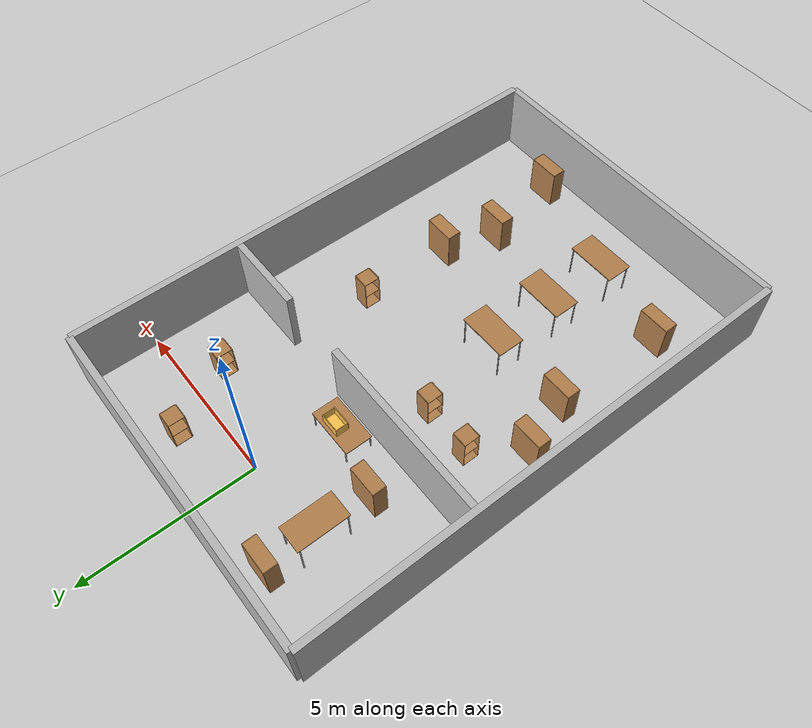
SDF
<sdf version="1.6">
 <world name="default">
  <physics name="default_physics" default="0" type="ode">
   <ode>
    <solver>
     <type>quick</type>
     <iters>20</iters>
     <sor>1</sor>
     <use_dynamic_moi_rescaling>0</use_dynamic_moi_rescaling>
    </solver>
    <constraints>
     <cfm>0</cfm>
     <erp>0.2</erp>
     <contact_max_correcting_vel>100</contact_max_correcting_vel>
     <contact_surface_layer>0</contact_surface_layer>
    </constraints>
   </ode>
   <real_time_update_rate>1000</real_time_update_rate>
   <max_step_size>0.001</max_step_size>
   <real_time_factor>1</real_time_factor>
   <max_contacts>20</max_contacts>
  </physics>
  <light name="sun" type="directional">
   <pose>0 0 10 0 -0 0</pose>
   <diffuse>0.8 0.8 0.8 1</diffuse>
   <specular>0.2 0.2 0.2 1</specular>
   <attenuation>
    <range>1000</range>
    <constant>0.9</constant>
    <linear>0.01</linear>
    <quadratic>0.001</quadratic>
   </attenuation>
   <direction>0.5 0.1 -0.9</direction>
  </light>
  <model name="ground_plane">
   <static>1</static>
   <link name="link">
    <collision name="collision">
     <geometry><plane><normal>0 0 1</normal><size>100 100</size></plane></geometry>
     <surface><friction><ode><mu>100</mu><mu2>50</mu2></ode></friction></surface>
    </collision>
    <visual name="visual">
     <cast_shadows>0</cast_shadows>
     <geometry><plane><normal>0 0 1</normal><size>100 100</size></plane></geometry>
     <material>
      <script><uri>file://media/materials/scripts/gazebo.material</uri><name>Gazebo/Grey</name></script>
     </material>
    </visual>
    <velocity_decay><linear>0</linear><angular>0</angular></velocity_decay>
   </link>
  </model>
  <model name="wall_1_model">
   <pose>0 -13 1 0 -0 0</pose>
   <static>1</static>
   <link name="wall_1_body">
    <inertial>
     <mass>1</mass>
     <inertia><ixx>1</ixx><ixy>0</ixy><ixz>0</ixz><iyy>1</iyy><iyz>0</iyz><izz>1</izz></inertia>
    </inertial>
    <collision name="collision"><geometry><box><size>10 0.2 2</size></box></geometry></collision>
    <visual name="visual"><geometry><box><size>10 0.2 2</size></box></geometry></visual>
    <velocity_decay><linear>0</linear><angular>0</angular></velocity_decay>
   </link>
  </model>
  <model name="wall_2_model">
   <pose>0 2 1 0 -0 0</pose>
   <static>1</static>
   <link name="wall_2_body">
    <inertial>
     <mass>1</mass>
     <inertia><ixx>1</ixx><ixy>0</ixy><ixz>0</ixz><iyy>1</iyy><iyz>0</iyz><izz>1</izz></inertia>
    </inertial>
    <collision name="collision"><geometry><box><size>10 0.2 2</size></box></geometry></collision>
    <visual name="visual"><geometry><box><size>10 0.2 2</size></box></geometry></visual>
    <velocity_decay><linear>0</linear><angular>0</angular></velocity_decay>
   </link>
  </model>
  <model name="wall_3_model">
   <pose>-5 -5.5 1 0 -0 0</pose>
   <static>1</static>
   <link name="wall_3_body">
    <inertial>
     <mass>1</mass>
     <inertia><ixx>1</ixx><ixy>0</ixy><ixz>0</ixz><iyy>1</iyy><iyz>0</iyz><izz>1</izz></inertia>
    </inertial>
    <collision name="collision"><geometry><box><size>0.2 15 2</size></box></geometry></collision>
    <visual name="visual"><geometry><box><size>0.2 15 2</size></box></geometry></visual>
    <velocity_decay><linear>0</linear><angular>0</angular></velocity_decay>
   </link>
  </model>
  <model name="wall_4_model">
   <pose>5 -5.5 1 0 -0 0</pose>
   <static>1</static>
   <link name="wall_4_body">
    <inertial>
     <mass>1</mass>
     <inertia><ixx>1</ixx><ixy>0</ixy><ixz>0</ixz><iyy>1</iyy><iyz>0</iyz><izz>1</izz></inertia>
    </inertial>
    <collision name="collision"><geometry><box><size>0.2 15 2</size></box></geometry></collision>
    <visual name="visual"><geometry><box><size>0.2 15 2</size></box></geometry></visual>
    <velocity_decay><linear>0</linear><angular>0</angular></velocity_decay>
   </link>
  </model>
  <model name="wall_5_model">
   <pose>-2.25 -3 1 0 -0 0</pose>
   <static>1</static>
   <link name="wall_5_body">
    <inertial>
     <mass>1</mass>
     <inertia><ixx>1</ixx><ixy>0</ixy><ixz>0</ixz><iyy>1</iyy><iyz>0</iyz><izz>1</izz></inertia>
    </inertial>
    <collision name="collision"><geometry><box><size>5.5 0.2 2</size></box></geometry></collision>
    <visual name="visual"><geometry><box><size>5.5 0.2 2</size></box></geometry></visual>
    <velocity_decay><linear>0</linear><angular>0</angular></velocity_decay>
   </link>
  </model>
  <model name="wall_6_model">
   <pose>3.75 -3 1 0 -0 0</pose>
   <static>1</static>
   <link name="wall_6_body">
    <inertial>
     <mass>1</mass>
     <inertia><ixx>1</ixx><ixy>0</ixy><ixz>0</ixz><iyy>1</iyy><iyz>0</iyz><izz>1</izz></inertia>
    </inertial>
    <collision name="collision"><geometry><box><size>2.5 0.2 2</size></box></geometry></collision>
    <visual name="visual"><geometry><box><size>2.5 0.2 2</size></box></geometry></visual>
    <velocity_decay><linear>0</linear><angular>0</angular></velocity_decay>
   </link>
  </model>
  <scene><ambient>0.2 0.2 0.2 1</ambient><background>0.7 0.7 0.7 1</background><shadows>1</shadows></scene>
  <model name="cabinet">
   <static>1</static>
   <link name="cabinet_bottom_plate">
    <inertial>
     <pose>0 0 -1 0 -0 0</pose>
     <inertia><ixx>2.05</ixx><ixy>0</ixy><ixz>0</ixz><iyy>2.05</iyy><iyz>0</iyz><izz>2.05</izz></inertia>
     <mass>25</mass>
    </inertial>
    <collision name="cabinet_bottom_plate_geom">
     <pose>0 0 0.01 0 -0 0</pose>
     <geometry><box><size>0.45 0.45 0.02</size></box></geometry>
    </collision>
    <visual name="cabinet_bottom_plate_geom_visual">
     <pose>0 0 0.01 0 -0 0</pose>
     <geometry><box><size>0.45 0.45 0.02</size></box></geometry>
     <material>
      <script><uri>file://media/materials/scripts/gazebo.material</uri><name>Gazebo/Wood</name></script>
     </material>
    </visual>
    <collision name="cabinet_bottom_plate_geom_cabinet_back_plate">
     <pose>0.235 0 0.51 0 -0 0</pose>
     <geometry><box><size>0.02 0.45 1.02</size></box></geometry>
    </collision>
    <visual name="cabinet_bottom_plate_geom_cabinet_back_plate_visual">
     <pose>0.235 0 0.51 0 -0 0</pose>
     <geometry><box><size>0.02 0.45 1.02</size></box></geometry>
     <material>
      <script><uri>file://media/materials/scripts/gazebo.material</uri><name>Gazebo/Wood</name></script>
     </material>
    </visual>
    <collision name="cabinet_bottom_plate_geom_cabinet_left_plate">
     <pose>0 0.235 0.51 0 -0 0</pose>
     <geometry><box><size>0.45 0.02 1.02</size></box></geometry>
    </collision>
    <visual name="cabinet_bottom_plate_geom_cabinet_left_plate_visual">
     <pose>0 0.235 0.51 0 -0 0</pose>
     <geometry><box><size>0.45 0.02 1.02</size></box></geometry>
     <material>
      <script><uri>file://media/materials/scripts/gazebo.material</uri><name>Gazebo/Wood</name></script>
     </material>
    </visual>
    <collision name="cabinet_bottom_plate_geom_cabinet_middle_plate">
     <pose>0 0 0.51 0 -0 0</pose>
     <geometry><box><size>0.45 0.45 0.02</size></box></geometry>
    </collision>
    <visual name="cabinet_bottom_plate_geom_cabinet_middle_plate_visual">
     <pose>0 0 0.51 0 -0 0</pose>
     <geometry><box><size>0.45 0.45 0.02</size></box></geometry>
     <material>
      <script><uri>file://media/materials/scripts/gazebo.material</uri><name>Gazebo/Wood</name></script>
     </material>
    </visual>
    <collision name="cabinet_bottom_plate_geom_cabinet_right_plate">
     <pose>0 -0.235 0.51 0 -0 0</pose>
     <geometry><box><size>0.45 0.02 1.02</size></box></geometry>
    </collision>
    <visual name="cabinet_bottom_plate_geom_cabinet_right_plate_visual">
     <pose>0 -0.235 0.51 0 -0 0</pose>
     <geometry><box><size>0.45 0.02 1.02</size></box></geometry>
     <material>
      <script><uri>file://media/materials/scripts/gazebo.material</uri><name>Gazebo/Wood</name></script>
     </material>
    </visual>
    <collision name="cabinet_bottom_plate_geom_cabinet_top_plate">
     <pose>0 0 1.01 0 -0 0</pose>
     <geometry><box><size>0.45 0.45 0.02</size></box></geometry>
    </collision>
    <visual name="cabinet_bottom_plate_geom_cabinet_top_plate_visual">
     <pose>0 0 1.01 0 -0 0</pose>
     <geometry><box><size>0.45 0.45 0.02</size></box></geometry>
     <material>
      <script><uri>file://media/materials/scripts/gazebo.material</uri><name>Gazebo/Wood</name></script>
     </material>
    </visual>
    <velocity_decay><linear>0</linear><angular>0</angular></velocity_decay>
   </link>
   <pose>2 1 0 0 -0 0</pose>
  </model>
  <model name="cabinet_0">
   <static>1</static>
   <link name="cabinet_bottom_plate">
    <inertial>
     <pose>0 0 -1 0 -0 0</pose>
     <inertia><ixx>2.05</ixx><ixy>0</ixy><ixz>0</ixz><iyy>2.05</iyy><iyz>0</iyz><izz>2.05</izz></inertia>
     <mass>25</mass>
    </inertial>
    <collision name="cabinet_bottom_plate_geom">
     <pose>0 0 0.01 0 -0 0</pose>
     <geometry><box><size>0.45 0.45 0.02</size></box></geometry>
    </collision>
    <visual name="cabinet_bottom_plate_geom_visual">
     <pose>0 0 0.01 0 -0 0</pose>
     <geometry><box><size>0.45 0.45 0.02</size></box></geometry>
     <material>
      <script><uri>file://media/materials/scripts/gazebo.material</uri><name>Gazebo/Wood</name></script>
     </material>
    </visual>
    <collision name="cabinet_bottom_plate_geom_cabinet_back_plate">
     <pose>0.235 0 0.51 0 -0 0</pose>
     <geometry><box><size>0.02 0.45 1.02</size></box></geometry>
    </collision>
    <visual name="cabinet_bottom_plate_geom_cabinet_back_plate_visual">
     <pose>0.235 0 0.51 0 -0 0</pose>
     <geometry><box><size>0.02 0.45 1.02</size></box></geometry>
     <material>
      <script><uri>file://media/materials/scripts/gazebo.material</uri><name>Gazebo/Wood</name></script>
     </material>
    </visual>
    <collision name="cabinet_bottom_plate_geom_cabinet_left_plate">
     <pose>0 0.235 0.51 0 -0 0</pose>
     <geometry><box><size>0.45 0.02 1.02</size></box></geometry>
    </collision>
    <visual name="cabinet_bottom_plate_geom_cabinet_left_plate_visual">
     <pose>0 0.235 0.51 0 -0 0</pose>
     <geometry><box><size>0.45 0.02 1.02</size></box></geometry>
     <material>
      <script><uri>file://media/materials/scripts/gazebo.material</uri><name>Gazebo/Wood</name></script>
     </material>
    </visual>
    <collision name="cabinet_bottom_plate_geom_cabinet_middle_plate">
     <pose>0 0 0.51 0 -0 0</pose>
     <geometry><box><size>0.45 0.45 0.02</size></box></geometry>
    </collision>
    <visual name="cabinet_bottom_plate_geom_cabinet_middle_plate_visual">
     <pose>0 0 0.51 0 -0 0</pose>
     <geometry><box><size>0.45 0.45 0.02</size></box></geometry>
     <material>
      <script><uri>file://media/materials/scripts/gazebo.material</uri><name>Gazebo/Wood</name></script>
     </material>
    </visual>
    <collision name="cabinet_bottom_plate_geom_cabinet_right_plate">
     <pose>0 -0.235 0.51 0 -0 0</pose>
     <geometry><box><size>0.45 0.02 1.02</size></box></geometry>
    </collision>
    <visual name="cabinet_bottom_plate_geom_cabinet_right_plate_visual">
     <pose>0 -0.235 0.51 0 -0 0</pose>
     <geometry><box><size>0.45 0.02 1.02</size></box></geometry>
     <material>
      <script><uri>file://media/materials/scripts/gazebo.material</uri><name>Gazebo/Wood</name></script>
     </material>
    </visual>
    <collision name="cabinet_bottom_plate_geom_cabinet_top_plate">
     <pose>0 0 1.01 0 -0 0</pose>
     <geometry><box><size>0.45 0.45 0.02</size></box></geometry>
    </collision>
    <visual name="cabinet_bottom_plate_geom_cabinet_top_plate_visual">
     <pose>0 0 1.01 0 -0 0</pose>
     <geometry><box><size>0.45 0.45 0.02</size></box></geometry>
     <material>
      <script><uri>file://media/materials/scripts/gazebo.material</uri><name>Gazebo/Wood</name></script>
     </material>
    </visual>
    <velocity_decay><linear>0</linear><angular>0</angular></velocity_decay>
   </link>
   <pose>2.51573 -5.43949 0 0 -0 0</pose>
  </model>
  <model name="bookshelf">
   <static>1</static>
   <link name="link">
    <inertial><mass>1</mass></inertial>
    <collision name="back">
     <pose>0 0.005 0.6 0 -0 0</pose>
     <geometry><box><size>0.9 0.01 1.2</size></box></geometry>
    </collision>
    <visual name="visual1">
     <pose>0 0.005 0.6 0 -0 0</pose>
     <geometry><box><size>0.9 0.01 1.2</size></box></geometry>
     <material>
      <script><uri>file://media/materials/scripts/gazebo.material</uri><name>Gazebo/Wood</name></script>
     </material>
    </visual>
    <collision name="left_side">
     <pose>0.45 -0.195 0.6 0 -0 0</pose>
     <geometry><box><size>0.02 0.4 1.2</size></box></geometry>
    </collision>
    <visual name="visual2">
     <pose>0.45 -0.195 0.6 0 -0 0</pose>
     <geometry><box><size>0.02 0.4 1.2</size></box></geometry>
     <material>
      <script><uri>file://media/materials/scripts/gazebo.material</uri><name>Gazebo/Wood</name></script>
     </material>
    </visual>
    <collision name="right_side">
     <pose>-0.45 -0.195 0.6 0 -0 0</pose>
     <geometry><box><size>0.02 0.4 1.2</size></box></geometry>
    </collision>
    <visual name="visual3">
     <pose>-0.45 -0.195 0.6 0 -0 0</pose>
     <geometry><box><size>0.02 0.4 1.2</size></box></geometry>
     <material>
      <script><uri>file://media/materials/scripts/gazebo.material</uri><name>Gazebo/Wood</name></script>
     </material>
    </visual>
    <collision name="bottom">
     <pose>0 -0.195 0.03 0 -0 0</pose>
     <geometry><box><size>0.88 0.4 0.06</size></box></geometry>
    </collision>
    <visual name="visual4">
     <pose>0 -0.195 0.03 0 -0 0</pose>
     <geometry><box><size>0.88 0.4 0.06</size></box></geometry>
     <material>
      <script><uri>file://media/materials/scripts/gazebo.material</uri><name>Gazebo/Wood</name></script>
     </material>
    </visual>
    <collision name="top">
     <pose>0 -0.195 1.19 0 -0 0</pose>
     <geometry><box><size>0.88 0.4 0.02</size></box></geometry>
    </collision>
    <visual name="visual5">
     <pose>0 -0.195 1.19 0 -0 0</pose>
     <geometry><box><size>0.88 0.4 0.02</size></box></geometry>
     <material>
      <script><uri>file://media/materials/scripts/gazebo.material</uri><name>Gazebo/Wood</name></script>
     </material>
    </visual>
    <collision name="low_shelf">
     <pose>0 -0.195 0.43 0 -0 0</pose>
     <geometry><box><size>0.88 0.4 0.02</size></box></geometry>
    </collision>
    <visual name="visual6">
     <pose>0 -0.195 0.43 0 -0 0</pose>
     <geometry><box><size>0.88 0.4 0.02</size></box></geometry>
     <material>
      <script><uri>file://media/materials/scripts/gazebo.material</uri><name>Gazebo/Wood</name></script>
     </material>
    </visual>
    <collision name="high_shelf">
     <pose>0 -0.195 0.8 0 -0 0</pose>
     <geometry><box><size>0.88 0.4 0.02</size></box></geometry>
    </collision>
    <visual name="visual7">
     <pose>0 -0.195 0.8 0 -0 0</pose>
     <geometry><box><size>0.88 0.4 0.02</size></box></geometry>
     <material>
      <script><uri>file://media/materials/scripts/gazebo.material</uri><name>Gazebo/Wood</name></script>
     </material>
    </visual>
    <velocity_decay><linear>0</linear><angular>0</angular></velocity_decay>
   </link>
   <pose>2 -9.55401 0 0 -0 0</pose>
  </model>
  <model name="bookshelf_0">
   <static>1</static>
   <link name="link">
    <inertial><mass>1</mass></inertial>
    <collision name="back">
     <pose>0 0.005 0.6 0 -0 0</pose>
     <geometry><box><size>0.9 0.01 1.2</size></box></geometry>
    </collision>
    <visual name="visual1">
     <pose>0 0.005 0.6 0 -0 0</pose>
     <geometry><box><size>0.9 0.01 1.2</size></box></geometry>
     <material>
      <script><uri>file://media/materials/scripts/gazebo.material</uri><name>Gazebo/Wood</name></script>
     </material>
    </visual>
    <collision name="left_side">
     <pose>0.45 -0.195 0.6 0 -0 0</pose>
     <geometry><box><size>0.02 0.4 1.2</size></box></geometry>
    </collision>
    <visual name="visual2">
     <pose>0.45 -0.195 0.6 0 -0 0</pose>
     <geometry><box><size>0.02 0.4 1.2</size></box></geometry>
     <material>
      <script><uri>file://media/materials/scripts/gazebo.material</uri><name>Gazebo/Wood</name></script>
     </material>
    </visual>
    <collision name="right_side">
     <pose>-0.45 -0.195 0.6 0 -0 0</pose>
     <geometry><box><size>0.02 0.4 1.2</size></box></geometry>
    </collision>
    <visual name="visual3">
     <pose>-0.45 -0.195 0.6 0 -0 0</pose>
     <geometry><box><size>0.02 0.4 1.2</size></box></geometry>
     <material>
      <script><uri>file://media/materials/scripts/gazebo.material</uri><name>Gazebo/Wood</name></script>
     </material>
    </visual>
    <collision name="bottom">
     <pose>0 -0.195 0.03 0 -0 0</pose>
     <geometry><box><size>0.88 0.4 0.06</size></box></geometry>
    </collision>
    <visual name="visual4">
     <pose>0 -0.195 0.03 0 -0 0</pose>
     <geometry><box><size>0.88 0.4 0.06</size></box></geometry>
     <material>
      <script><uri>file://media/materials/scripts/gazebo.material</uri><name>Gazebo/Wood</name></script>
     </material>
    </visual>
    <collision name="top">
     <pose>0 -0.195 1.19 0 -0 0</pose>
     <geometry><box><size>0.88 0.4 0.02</size></box></geometry>
    </collision>
    <visual name="visual5">
     <pose>0 -0.195 1.19 0 -0 0</pose>
     <geometry><box><size>0.88 0.4 0.02</size></box></geometry>
     <material>
      <script><uri>file://media/materials/scripts/gazebo.material</uri><name>Gazebo/Wood</name></script>
     </material>
    </visual>
    <collision name="low_shelf">
     <pose>0 -0.195 0.43 0 -0 0</pose>
     <geometry><box><size>0.88 0.4 0.02</size></box></geometry>
    </collision>
    <visual name="visual6">
     <pose>0 -0.195 0.43 0 -0 0</pose>
     <geometry><box><size>0.88 0.4 0.02</size></box></geometry>
     <material>
      <script><uri>file://media/materials/scripts/gazebo.material</uri><name>Gazebo/Wood</name></script>
     </material>
    </visual>
    <collision name="high_shelf">
     <pose>0 -0.195 0.8 0 -0 0</pose>
     <geometry><box><size>0.88 0.4 0.02</size></box></geometry>
    </collision>
    <visual name="visual7">
     <pose>0 -0.195 0.8 0 -0 0</pose>
     <geometry><box><size>0.88 0.4 0.02</size></box></geometry>
     <material>
      <script><uri>file://media/materials/scripts/gazebo.material</uri><name>Gazebo/Wood</name></script>
     </material>
    </visual>
    <velocity_decay><linear>0</linear><angular>0</angular></velocity_decay>
   </link>
   <pose>-2.49657 -1.57894 0 0 -0 0</pose>
  </model>
  <model name="bookshelf_1">
   <static>1</static>
   <link name="link">
    <inertial><mass>1</mass></inertial>
    <collision name="back">
     <pose>0 0.005 0.6 0 -0 0</pose>
     <geometry><box><size>0.9 0.01 1.2</size></box></geometry>
    </collision>
    <visual name="visual1">
     <pose>0 0.005 0.6 0 -0 0</pose>
     <geometry><box><size>0.9 0.01 1.2</size></box></geometry>
     <material>
      <script><uri>file://media/materials/scripts/gazebo.material</uri><name>Gazebo/Wood</name></script>
     </material>
    </visual>
    <collision name="left_side">
     <pose>0.45 -0.195 0.6 0 -0 0</pose>
     <geometry><box><size>0.02 0.4 1.2</size></box></geometry>
    </collision>
    <visual name="visual2">
     <pose>0.45 -0.195 0.6 0 -0 0</pose>
     <geometry><box><size>0.02 0.4 1.2</size></box></geometry>
     <material>
      <script><uri>file://media/materials/scripts/gazebo.material</uri><name>Gazebo/Wood</name></script>
     </material>
    </visual>
    <collision name="right_side">
     <pose>-0.45 -0.195 0.6 0 -0 0</pose>
     <geometry><box><size>0.02 0.4 1.2</size></box></geometry>
    </collision>
    <visual name="visual3">
     <pose>-0.45 -0.195 0.6 0 -0 0</pose>
     <geometry><box><size>0.02 0.4 1.2</size></box></geometry>
     <material>
      <script><uri>file://media/materials/scripts/gazebo.material</uri><name>Gazebo/Wood</name></script>
     </material>
    </visual>
    <collision name="bottom">
     <pose>0 -0.195 0.03 0 -0 0</pose>
     <geometry><box><size>0.88 0.4 0.06</size></box></geometry>
    </collision>
    <visual name="visual4">
     <pose>0 -0.195 0.03 0 -0 0</pose>
     <geometry><box><size>0.88 0.4 0.06</size></box></geometry>
     <material>
      <script><uri>file://media/materials/scripts/gazebo.material</uri><name>Gazebo/Wood</name></script>
     </material>
    </visual>
    <collision name="top">
     <pose>0 -0.195 1.19 0 -0 0</pose>
     <geometry><box><size>0.88 0.4 0.02</size></box></geometry>
    </collision>
    <visual name="visual5">
     <pose>0 -0.195 1.19 0 -0 0</pose>
     <geometry><box><size>0.88 0.4 0.02</size></box></geometry>
     <material>
      <script><uri>file://media/materials/scripts/gazebo.material</uri><name>Gazebo/Wood</name></script>
     </material>
    </visual>
    <collision name="low_shelf">
     <pose>0 -0.195 0.43 0 -0 0</pose>
     <geometry><box><size>0.88 0.4 0.02</size></box></geometry>
    </collision>
    <visual name="visual6">
     <pose>0 -0.195 0.43 0 -0 0</pose>
     <geometry><box><size>0.88 0.4 0.02</size></box></geometry>
     <material>
      <script><uri>file://media/materials/scripts/gazebo.material</uri><name>Gazebo/Wood</name></script>
     </material>
    </visual>
    <collision name="high_shelf">
     <pose>0 -0.195 0.8 0 -0 0</pose>
     <geometry><box><size>0.88 0.4 0.02</size></box></geometry>
    </collision>
    <visual name="visual7">
     <pose>0 -0.195 0.8 0 -0 0</pose>
     <geometry><box><size>0.88 0.4 0.02</size></box></geometry>
     <material>
      <script><uri>file://media/materials/scripts/gazebo.material</uri><name>Gazebo/Wood</name></script>
     </material>
    </visual>
    <velocity_decay><linear>0</linear><angular>0</angular></velocity_decay>
   </link>
   <pose>-2.49816 1.46785 0 0 -0 0</pose>
  </model>
  <model name="table">
   <static>1</static>
   <link name="link">
    <collision name="surface">
     <pose>0 0 1 0 -0 0</pose>
     <geometry><box><size>1.5 0.8 0.03</size></box></geometry>
    </collision>
    <visual name="visual1">
     <pose>0 0 1 0 -0 0</pose>
     <geometry><box><size>1.5 0.8 0.03</size></box></geometry>
     <material>
      <script><uri>file://media/materials/scripts/gazebo.material</uri><name>Gazebo/Wood</name></script>
     </material>
    </visual>
    <collision name="front_left_leg">
     <pose>0.68 0.38 0.5 0 -0 0</pose>
     <geometry><cylinder><radius>0.02</radius><length>1</length></cylinder></geometry>
    </collision>
    <visual name="front_left_leg">
     <pose>0.68 0.38 0.5 0 -0 0</pose>
     <geometry><cylinder><radius>0.02</radius><length>1</length></cylinder></geometry>
     <material>
      <script><uri>file://media/materials/scripts/gazebo.material</uri><name>Gazebo/Grey</name></script>
     </material>
    </visual>
    <collision name="front_right_leg">
     <pose>0.68 -0.38 0.5 0 -0 0</pose>
     <geometry><cylinder><radius>0.02</radius><length>1</length></cylinder></geometry>
    </collision>
    <visual name="front_right_leg">
     <pose>0.68 -0.38 0.5 0 -0 0</pose>
     <geometry><cylinder><radius>0.02</radius><length>1</length></cylinder></geometry>
     <material>
      <script><uri>file://media/materials/scripts/gazebo.material</uri><name>Gazebo/Grey</name></script>
     </material>
    </visual>
    <collision name="back_right_leg">
     <pose>-0.68 -0.38 0.5 0 -0 0</pose>
     <geometry><cylinder><radius>0.02</radius><length>1</length></cylinder></geometry>
    </collision>
    <visual name="back_right_leg">
     <pose>-0.68 -0.38 0.5 0 -0 0</pose>
     <geometry><cylinder><radius>0.02</radius><length>1</length></cylinder></geometry>
     <material>
      <script><uri>file://media/materials/scripts/gazebo.material</uri><name>Gazebo/Grey</name></script>
     </material>
    </visual>
    <collision name="back_left_leg">
     <pose>-0.68 0.38 0.5 0 -0 0</pose>
     <geometry><cylinder><radius>0.02</radius><length>1</length></cylinder></geometry>
    </collision>
    <visual name="back_left_leg">
     <pose>-0.68 0.38 0.5 0 -0 0</pose>
     <geometry><cylinder><radius>0.02</radius><length>1</length></cylinder></geometry>
     <material>
      <script><uri>file://media/materials/scripts/gazebo.material</uri><name>Gazebo/Grey</name></script>
     </material>
    </visual>
    <velocity_decay><linear>0</linear><angular>0</angular></velocity_decay>
   </link>
   <pose>-1 -9 0 0 -0 0</pose>
  </model>
  <model name="cabinet_1">
   <static>1</static>
   <link name="cabinet_bottom_plate">
    <inertial>
     <pose>0 0 -1 0 -0 0</pose>
     <inertia><ixx>2.05</ixx><ixy>0</ixy><ixz>0</ixz><iyy>2.05</iyy><iyz>0</iyz><izz>2.05</izz></inertia>
     <mass>25</mass>
    </inertial>
    <collision name="cabinet_bottom_plate_geom">
     <pose>0 0 0.01 0 -0 0</pose>
     <geometry><box><size>0.45 0.45 0.02</size></box></geometry>
    </collision>
    <visual name="cabinet_bottom_plate_geom_visual">
     <pose>0 0 0.01 0 -0 0</pose>
     <geometry><box><size>0.45 0.45 0.02</size></box></geometry>
     <material>
      <script><uri>file://media/materials/scripts/gazebo.material</uri><name>Gazebo/Wood</name></script>
     </material>
    </visual>
    <collision name="cabinet_bottom_plate_geom_cabinet_back_plate">
     <pose>0.235 0 0.51 0 -0 0</pose>
     <geometry><box><size>0.02 0.45 1.02</size></box></geometry>
    </collision>
    <visual name="cabinet_bottom_plate_geom_cabinet_back_plate_visual">
     <pose>0.235 0 0.51 0 -0 0</pose>
     <geometry><box><size>0.02 0.45 1.02</size></box></geometry>
     <material>
      <script><uri>file://media/materials/scripts/gazebo.material</uri><name>Gazebo/Wood</name></script>
     </material>
    </visual>
    <collision name="cabinet_bottom_plate_geom_cabinet_left_plate">
     <pose>0 0.235 0.51 0 -0 0</pose>
     <geometry><box><size>0.45 0.02 1.02</size></box></geometry>
    </collision>
    <visual name="cabinet_bottom_plate_geom_cabinet_left_plate_visual">
     <pose>0 0.235 0.51 0 -0 0</pose>
     <geometry><box><size>0.45 0.02 1.02</size></box></geometry>
     <material>
      <script><uri>file://media/materials/scripts/gazebo.material</uri><name>Gazebo/Wood</name></script>
     </material>
    </visual>
    <collision name="cabinet_bottom_plate_geom_cabinet_middle_plate">
     <pose>0 0 0.51 0 -0 0</pose>
     <geometry><box><size>0.45 0.45 0.02</size></box></geometry>
    </collision>
    <visual name="cabinet_bottom_plate_geom_cabinet_middle_plate_visual">
     <pose>0 0 0.51 0 -0 0</pose>
     <geometry><box><size>0.45 0.45 0.02</size></box></geometry>
     <material>
      <script><uri>file://media/materials/scripts/gazebo.material</uri><name>Gazebo/Wood</name></script>
     </material>
    </visual>
    <collision name="cabinet_bottom_plate_geom_cabinet_right_plate">
     <pose>0 -0.235 0.51 0 -0 0</pose>
     <geometry><box><size>0.45 0.02 1.02</size></box></geometry>
    </collision>
    <visual name="cabinet_bottom_plate_geom_cabinet_right_plate_visual">
     <pose>0 -0.235 0.51 0 -0 0</pose>
     <geometry><box><size>0.45 0.02 1.02</size></box></geometry>
     <material>
      <script><uri>file://media/materials/scripts/gazebo.material</uri><name>Gazebo/Wood</name></script>
     </material>
    </visual>
    <collision name="cabinet_bottom_plate_geom_cabinet_top_plate">
     <pose>0 0 1.01 0 -0 0</pose>
     <geometry><box><size>0.45 0.45 0.02</size></box></geometry>
    </collision>
    <visual name="cabinet_bottom_plate_geom_cabinet_top_plate_visual">
     <pose>0 0 1.01 0 -0 0</pose>
     <geometry><box><size>0.45 0.45 0.02</size></box></geometry>
     <material>
      <script><uri>file://media/materials/scripts/gazebo.material</uri><name>Gazebo/Wood</name></script>
     </material>
    </visual>
    <velocity_decay><linear>0</linear><angular>0</angular></velocity_decay>
   </link>
   <pose>-3 -4.40005 0 0 -0 0</pose>
  </model>
  <model name="cabinet_2">
   <static>1</static>
   <link name="cabinet_bottom_plate">
    <inertial>
     <pose>0 0 -1 0 -0 0</pose>
     <inertia><ixx>2.05</ixx><ixy>0</ixy><ixz>0</ixz><iyy>2.05</iyy><iyz>0</iyz><izz>2.05</izz></inertia>
     <mass>25</mass>
    </inertial>
    <collision name="cabinet_bottom_plate_geom">
     <pose>0 0 0.01 0 -0 0</pose>
     <geometry><box><size>0.45 0.45 0.02</size></box></geometry>
    </collision>
    <visual name="cabinet_bottom_plate_geom_visual">
     <pose>0 0 0.01 0 -0 0</pose>
     <geometry><box><size>0.45 0.45 0.02</size></box></geometry>
     <material>
      <script><uri>file://media/materials/scripts/gazebo.material</uri><name>Gazebo/Wood</name></script>
     </material>
    </visual>
    <collision name="cabinet_bottom_plate_geom_cabinet_back_plate">
     <pose>0.235 0 0.51 0 -0 0</pose>
     <geometry><box><size>0.02 0.45 1.02</size></box></geometry>
    </collision>
    <visual name="cabinet_bottom_plate_geom_cabinet_back_plate_visual">
     <pose>0.235 0 0.51 0 -0 0</pose>
     <geometry><box><size>0.02 0.45 1.02</size></box></geometry>
     <material>
      <script><uri>file://media/materials/scripts/gazebo.material</uri><name>Gazebo/Wood</name></script>
     </material>
    </visual>
    <collision name="cabinet_bottom_plate_geom_cabinet_left_plate">
     <pose>0 0.235 0.51 0 -0 0</pose>
     <geometry><box><size>0.45 0.02 1.02</size></box></geometry>
    </collision>
    <visual name="cabinet_bottom_plate_geom_cabinet_left_plate_visual">
     <pose>0 0.235 0.51 0 -0 0</pose>
     <geometry><box><size>0.45 0.02 1.02</size></box></geometry>
     <material>
      <script><uri>file://media/materials/scripts/gazebo.material</uri><name>Gazebo/Wood</name></script>
     </material>
    </visual>
    <collision name="cabinet_bottom_plate_geom_cabinet_middle_plate">
     <pose>0 0 0.51 0 -0 0</pose>
     <geometry><box><size>0.45 0.45 0.02</size></box></geometry>
    </collision>
    <visual name="cabinet_bottom_plate_geom_cabinet_middle_plate_visual">
     <pose>0 0 0.51 0 -0 0</pose>
     <geometry><box><size>0.45 0.45 0.02</size></box></geometry>
     <material>
      <script><uri>file://media/materials/scripts/gazebo.material</uri><name>Gazebo/Wood</name></script>
     </material>
    </visual>
    <collision name="cabinet_bottom_plate_geom_cabinet_right_plate">
     <pose>0 -0.235 0.51 0 -0 0</pose>
     <geometry><box><size>0.45 0.02 1.02</size></box></geometry>
    </collision>
    <visual name="cabinet_bottom_plate_geom_cabinet_right_plate_visual">
     <pose>0 -0.235 0.51 0 -0 0</pose>
     <geometry><box><size>0.45 0.02 1.02</size></box></geometry>
     <material>
      <script><uri>file://media/materials/scripts/gazebo.material</uri><name>Gazebo/Wood</name></script>
     </material>
    </visual>
    <collision name="cabinet_bottom_plate_geom_cabinet_top_plate">
     <pose>0 0 1.01 0 -0 0</pose>
     <geometry><box><size>0.45 0.45 0.02</size></box></geometry>
    </collision>
    <visual name="cabinet_bottom_plate_geom_cabinet_top_plate_visual">
     <pose>0 0 1.01 0 -0 0</pose>
     <geometry><box><size>0.45 0.45 0.02</size></box></geometry>
     <material>
      <script><uri>file://media/materials/scripts/gazebo.material</uri><name>Gazebo/Wood</name></script>
     </material>
    </visual>
    <velocity_decay><linear>0</linear><angular>0</angular></velocity_decay>
   </link>
   <pose>-1.49183 -4.45622 0 0 -0 0</pose>
  </model>
  <model name="bookshelf_2">
   <static>1</static>
   <link name="link">
    <inertial><mass>1</mass></inertial>
    <collision name="back">
     <pose>0 0.005 0.6 0 -0 0</pose>
     <geometry><box><size>0.9 0.01 1.2</size></box></geometry>
    </collision>
    <visual name="visual1">
     <pose>0 0.005 0.6 0 -0 0</pose>
     <geometry><box><size>0.9 0.01 1.2</size></box></geometry>
     <material>
      <script><uri>file://media/materials/scripts/gazebo.material</uri><name>Gazebo/Wood</name></script>
     </material>
    </visual>
    <collision name="left_side">
     <pose>0.45 -0.195 0.6 0 -0 0</pose>
     <geometry><box><size>0.02 0.4 1.2</size></box></geometry>
    </collision>
    <visual name="visual2">
     <pose>0.45 -0.195 0.6 0 -0 0</pose>
     <geometry><box><size>0.02 0.4 1.2</size></box></geometry>
     <material>
      <script><uri>file://media/materials/scripts/gazebo.material</uri><name>Gazebo/Wood</name></script>
     </material>
    </visual>
    <collision name="right_side">
     <pose>-0.45 -0.195 0.6 0 -0 0</pose>
     <geometry><box><size>0.02 0.4 1.2</size></box></geometry>
    </collision>
    <visual name="visual3">
     <pose>-0.45 -0.195 0.6 0 -0 0</pose>
     <geometry><box><size>0.02 0.4 1.2</size></box></geometry>
     <material>
      <script><uri>file://media/materials/scripts/gazebo.material</uri><name>Gazebo/Wood</name></script>
     </material>
    </visual>
    <collision name="bottom">
     <pose>0 -0.195 0.03 0 -0 0</pose>
     <geometry><box><size>0.88 0.4 0.06</size></box></geometry>
    </collision>
    <visual name="visual4">
     <pose>0 -0.195 0.03 0 -0 0</pose>
     <geometry><box><size>0.88 0.4 0.06</size></box></geometry>
     <material>
      <script><uri>file://media/materials/scripts/gazebo.material</uri><name>Gazebo/Wood</name></script>
     </material>
    </visual>
    <collision name="top">
     <pose>0 -0.195 1.19 0 -0 0</pose>
     <geometry><box><size>0.88 0.4 0.02</size></box></geometry>
    </collision>
    <visual name="visual5">
     <pose>0 -0.195 1.19 0 -0 0</pose>
     <geometry><box><size>0.88 0.4 0.02</size></box></geometry>
     <material>
      <script><uri>file://media/materials/scripts/gazebo.material</uri><name>Gazebo/Wood</name></script>
     </material>
    </visual>
    <collision name="low_shelf">
     <pose>0 -0.195 0.43 0 -0 0</pose>
     <geometry><box><size>0.88 0.4 0.02</size></box></geometry>
    </collision>
    <visual name="visual6">
     <pose>0 -0.195 0.43 0 -0 0</pose>
     <geometry><box><size>0.88 0.4 0.02</size></box></geometry>
     <material>
      <script><uri>file://media/materials/scripts/gazebo.material</uri><name>Gazebo/Wood</name></script>
     </material>
    </visual>
    <collision name="high_shelf">
     <pose>0 -0.195 0.8 0 -0 0</pose>
     <geometry><box><size>0.88 0.4 0.02</size></box></geometry>
    </collision>
    <visual name="visual7">
     <pose>0 -0.195 0.8 0 -0 0</pose>
     <geometry><box><size>0.88 0.4 0.02</size></box></geometry>
     <material>
      <script><uri>file://media/materials/scripts/gazebo.material</uri><name>Gazebo/Wood</name></script>
     </material>
    </visual>
    <velocity_decay><linear>0</linear><angular>0</angular></velocity_decay>
   </link>
   <pose>-3.41849 -7 0 0 -0 0</pose>
  </model>
  <model name="table_0">
   <static>1</static>
   <link name="link">
    <collision name="surface">
     <pose>0 0 1 0 -0 0</pose>
     <geometry><box><size>1.5 0.8 0.03</size></box></geometry>
    </collision>
    <visual name="visual1">
     <pose>0 0 1 0 -0 0</pose>
     <geometry><box><size>1.5 0.8 0.03</size></box></geometry>
     <material>
      <script><uri>file://media/materials/scripts/gazebo.material</uri><name>Gazebo/Wood</name></script>
     </material>
    </visual>
    <collision name="front_left_leg">
     <pose>0.68 0.38 0.5 0 -0 0</pose>
     <geometry><cylinder><radius>0.02</radius><length>1</length></cylinder></geometry>
    </collision>
    <visual name="front_left_leg">
     <pose>0.68 0.38 0.5 0 -0 0</pose>
     <geometry><cylinder><radius>0.02</radius><length>1</length></cylinder></geometry>
     <material>
      <script><uri>file://media/materials/scripts/gazebo.material</uri><name>Gazebo/Grey</name></script>
     </material>
    </visual>
    <collision name="front_right_leg">
     <pose>0.68 -0.38 0.5 0 -0 0</pose>
     <geometry><cylinder><radius>0.02</radius><length>1</length></cylinder></geometry>
    </collision>
    <visual name="front_right_leg">
     <pose>0.68 -0.38 0.5 0 -0 0</pose>
     <geometry><cylinder><radius>0.02</radius><length>1</length></cylinder></geometry>
     <material>
      <script><uri>file://media/materials/scripts/gazebo.material</uri><name>Gazebo/Grey</name></script>
     </material>
    </visual>
    <collision name="back_right_leg">
     <pose>-0.68 -0.38 0.5 0 -0 0</pose>
     <geometry><cylinder><radius>0.02</radius><length>1</length></cylinder></geometry>
    </collision>
    <visual name="back_right_leg">
     <pose>-0.68 -0.38 0.5 0 -0 0</pose>
     <geometry><cylinder><radius>0.02</radius><length>1</length></cylinder></geometry>
     <material>
      <script><uri>file://media/materials/scripts/gazebo.material</uri><name>Gazebo/Grey</name></script>
     </material>
    </visual>
    <collision name="back_left_leg">
     <pose>-0.68 0.38 0.5 0 -0 0</pose>
     <geometry><cylinder><radius>0.02</radius><length>1</length></cylinder></geometry>
    </collision>
    <visual name="back_left_leg">
     <pose>-0.68 0.38 0.5 0 -0 0</pose>
     <geometry><cylinder><radius>0.02</radius><length>1</length></cylinder></geometry>
     <material>
      <script><uri>file://media/materials/scripts/gazebo.material</uri><name>Gazebo/Grey</name></script>
     </material>
    </visual>
    <velocity_decay><linear>0</linear><angular>0</angular></velocity_decay>
   </link>
   <pose>-1 -7 0 0 -0 0</pose>
  </model>
  <model name="table_1">
   <static>1</static>
   <link name="link">
    <collision name="surface">
     <pose>0 0 1 0 -0 0</pose>
     <geometry><box><size>1.5 0.8 0.03</size></box></geometry>
    </collision>
    <visual name="visual1">
     <pose>0 0 1 0 -0 0</pose>
     <geometry><box><size>1.5 0.8 0.03</size></box></geometry>
     <material>
      <script><uri>file://media/materials/scripts/gazebo.material</uri><name>Gazebo/Wood</name></script>
     </material>
    </visual>
    <collision name="front_left_leg">
     <pose>0.68 0.38 0.5 0 -0 0</pose>
     <geometry><cylinder><radius>0.02</radius><length>1</length></cylinder></geometry>
    </collision>
    <visual name="front_left_leg">
     <pose>0.68 0.38 0.5 0 -0 0</pose>
     <geometry><cylinder><radius>0.02</radius><length>1</length></cylinder></geometry>
     <material>
      <script><uri>file://media/materials/scripts/gazebo.material</uri><name>Gazebo/Grey</name></script>
     </material>
    </visual>
    <collision name="front_right_leg">
     <pose>0.68 -0.38 0.5 0 -0 0</pose>
     <geometry><cylinder><radius>0.02</radius><length>1</length></cylinder></geometry>
    </collision>
    <visual name="front_right_leg">
     <pose>0.68 -0.38 0.5 0 -0 0</pose>
     <geometry><cylinder><radius>0.02</radius><length>1</length></cylinder></geometry>
     <material>
      <script><uri>file://media/materials/scripts/gazebo.material</uri><name>Gazebo/Grey</name></script>
     </material>
    </visual>
    <collision name="back_right_leg">
     <pose>-0.68 -0.38 0.5 0 -0 0</pose>
     <geometry><cylinder><radius>0.02</radius><length>1</length></cylinder></geometry>
    </collision>
    <visual name="back_right_leg">
     <pose>-0.68 -0.38 0.5 0 -0 0</pose>
     <geometry><cylinder><radius>0.02</radius><length>1</length></cylinder></geometry>
     <material>
      <script><uri>file://media/materials/scripts/gazebo.material</uri><name>Gazebo/Grey</name></script>
     </material>
    </visual>
    <collision name="back_left_leg">
     <pose>-0.68 0.38 0.5 0 -0 0</pose>
     <geometry><cylinder><radius>0.02</radius><length>1</length></cylinder></geometry>
    </collision>
    <visual name="back_left_leg">
     <pose>-0.68 0.38 0.5 0 -0 0</pose>
     <geometry><cylinder><radius>0.02</radius><length>1</length></cylinder></geometry>
     <material>
      <script><uri>file://media/materials/scripts/gazebo.material</uri><name>Gazebo/Grey</name></script>
     </material>
    </visual>
    <velocity_decay><linear>0</linear><angular>0</angular></velocity_decay>
   </link>
   <pose>-1 -11 0 0 -0 0</pose>
  </model>
  <model name="cabinet_3">
   <static>1</static>
   <link name="cabinet_bottom_plate">
    <inertial>
     <pose>0 0 -1 0 -0 0</pose>
     <inertia><ixx>2.05</ixx><ixy>0</ixy><ixz>0</ixz><iyy>2.05</iyy><iyz>0</iyz><izz>2.05</izz></inertia>
     <mass>25</mass>
    </inertial>
    <collision name="cabinet_bottom_plate_geom">
     <pose>0 0 0.01 0 -0 0</pose>
     <geometry><box><size>0.45 0.45 0.02</size></box></geometry>
    </collision>
    <visual name="cabinet_bottom_plate_geom_visual">
     <pose>0 0 0.01 0 -0 0</pose>
     <geometry><box><size>0.45 0.45 0.02</size></box></geometry>
     <material>
      <script><uri>file://media/materials/scripts/gazebo.material</uri><name>Gazebo/Wood</name></script>
     </material>
    </visual>
    <collision name="cabinet_bottom_plate_geom_cabinet_back_plate">
     <pose>0.235 0 0.51 0 -0 0</pose>
     <geometry><box><size>0.02 0.45 1.02</size></box></geometry>
    </collision>
    <visual name="cabinet_bottom_plate_geom_cabinet_back_plate_visual">
     <pose>0.235 0 0.51 0 -0 0</pose>
     <geometry><box><size>0.02 0.45 1.02</size></box></geometry>
     <material>
      <script><uri>file://media/materials/scripts/gazebo.material</uri><name>Gazebo/Wood</name></script>
     </material>
    </visual>
    <collision name="cabinet_bottom_plate_geom_cabinet_left_plate">
     <pose>0 0.235 0.51 0 -0 0</pose>
     <geometry><box><size>0.45 0.02 1.02</size></box></geometry>
    </collision>
    <visual name="cabinet_bottom_plate_geom_cabinet_left_plate_visual">
     <pose>0 0.235 0.51 0 -0 0</pose>
     <geometry><box><size>0.45 0.02 1.02</size></box></geometry>
     <material>
      <script><uri>file://media/materials/scripts/gazebo.material</uri><name>Gazebo/Wood</name></script>
     </material>
    </visual>
    <collision name="cabinet_bottom_plate_geom_cabinet_middle_plate">
     <pose>0 0 0.51 0 -0 0</pose>
     <geometry><box><size>0.45 0.45 0.02</size></box></geometry>
    </collision>
    <visual name="cabinet_bottom_plate_geom_cabinet_middle_plate_visual">
     <pose>0 0 0.51 0 -0 0</pose>
     <geometry><box><size>0.45 0.45 0.02</size></box></geometry>
     <material>
      <script><uri>file://media/materials/scripts/gazebo.material</uri><name>Gazebo/Wood</name></script>
     </material>
    </visual>
    <collision name="cabinet_bottom_plate_geom_cabinet_right_plate">
     <pose>0 -0.235 0.51 0 -0 0</pose>
     <geometry><box><size>0.45 0.02 1.02</size></box></geometry>
    </collision>
    <visual name="cabinet_bottom_plate_geom_cabinet_right_plate_visual">
     <pose>0 -0.235 0.51 0 -0 0</pose>
     <geometry><box><size>0.45 0.02 1.02</size></box></geometry>
     <material>
      <script><uri>file://media/materials/scripts/gazebo.material</uri><name>Gazebo/Wood</name></script>
     </material>
    </visual>
    <collision name="cabinet_bottom_plate_geom_cabinet_top_plate">
     <pose>0 0 1.01 0 -0 0</pose>
     <geometry><box><size>0.45 0.45 0.02</size></box></geometry>
    </collision>
    <visual name="cabinet_bottom_plate_geom_cabinet_top_plate_visual">
     <pose>0 0 1.01 0 -0 0</pose>
     <geometry><box><size>0.45 0.45 0.02</size></box></geometry>
     <material>
      <script><uri>file://media/materials/scripts/gazebo.material</uri><name>Gazebo/Wood</name></script>
     </material>
    </visual>
    <velocity_decay><linear>0</linear><angular>0</angular></velocity_decay>
   </link>
   <pose>3 -1 0 0 -0 0</pose>
  </model>
  <model name="bookshelf_3">
   <static>1</static>
   <link name="link">
    <inertial><mass>1</mass></inertial>
    <collision name="back">
     <pose>0 0.005 0.6 0 -0 0</pose>
     <geometry><box><size>0.9 0.01 1.2</size></box></geometry>
    </collision>
    <visual name="visual1">
     <pose>0 0.005 0.6 0 -0 0</pose>
     <geometry><box><size>0.9 0.01 1.2</size></box></geometry>
     <material>
      <script><uri>file://media/materials/scripts/gazebo.material</uri><name>Gazebo/Wood</name></script>
     </material>
    </visual>
    <collision name="left_side">
     <pose>0.45 -0.195 0.6 0 -0 0</pose>
     <geometry><box><size>0.02 0.4 1.2</size></box></geometry>
    </collision>
    <visual name="visual2">
     <pose>0.45 -0.195 0.6 0 -0 0</pose>
     <geometry><box><size>0.02 0.4 1.2</size></box></geometry>
     <material>
      <script><uri>file://media/materials/scripts/gazebo.material</uri><name>Gazebo/Wood</name></script>
     </material>
    </visual>
    <collision name="right_side">
     <pose>-0.45 -0.195 0.6 0 -0 0</pose>
     <geometry><box><size>0.02 0.4 1.2</size></box></geometry>
    </collision>
    <visual name="visual3">
     <pose>-0.45 -0.195 0.6 0 -0 0</pose>
     <geometry><box><size>0.02 0.4 1.2</size></box></geometry>
     <material>
      <script><uri>file://media/materials/scripts/gazebo.material</uri><name>Gazebo/Wood</name></script>
     </material>
    </visual>
    <collision name="bottom">
     <pose>0 -0.195 0.03 0 -0 0</pose>
     <geometry><box><size>0.88 0.4 0.06</size></box></geometry>
    </collision>
    <visual name="visual4">
     <pose>0 -0.195 0.03 0 -0 0</pose>
     <geometry><box><size>0.88 0.4 0.06</size></box></geometry>
     <material>
      <script><uri>file://media/materials/scripts/gazebo.material</uri><name>Gazebo/Wood</name></script>
     </material>
    </visual>
    <collision name="top">
     <pose>0 -0.195 1.19 0 -0 0</pose>
     <geometry><box><size>0.88 0.4 0.02</size></box></geometry>
    </collision>
    <visual name="visual5">
     <pose>0 -0.195 1.19 0 -0 0</pose>
     <geometry><box><size>0.88 0.4 0.02</size></box></geometry>
     <material>
      <script><uri>file://media/materials/scripts/gazebo.material</uri><name>Gazebo/Wood</name></script>
     </material>
    </visual>
    <collision name="low_shelf">
     <pose>0 -0.195 0.43 0 -0 0</pose>
     <geometry><box><size>0.88 0.4 0.02</size></box></geometry>
    </collision>
    <visual name="visual6">
     <pose>0 -0.195 0.43 0 -0 0</pose>
     <geometry><box><size>0.88 0.4 0.02</size></box></geometry>
     <material>
      <script><uri>file://media/materials/scripts/gazebo.material</uri><name>Gazebo/Wood</name></script>
     </material>
    </visual>
    <collision name="high_shelf">
     <pose>0 -0.195 0.8 0 -0 0</pose>
     <geometry><box><size>0.88 0.4 0.02</size></box></geometry>
    </collision>
    <visual name="visual7">
     <pose>0 -0.195 0.8 0 -0 0</pose>
     <geometry><box><size>0.88 0.4 0.02</size></box></geometry>
     <material>
      <script><uri>file://media/materials/scripts/gazebo.material</uri><name>Gazebo/Wood</name></script>
     </material>
    </visual>
    <velocity_decay><linear>0</linear><angular>0</angular></velocity_decay>
   </link>
   <pose>2.45055 -12 0 0 -0 0</pose>
  </model>
  <model name="bookshelf_4">
   <static>1</static>
   <link name="link">
    <inertial><mass>1</mass></inertial>
    <collision name="back">
     <pose>0 0.005 0.6 0 -0 0</pose>
     <geometry><box><size>0.9 0.01 1.2</size></box></geometry>
    </collision>
    <visual name="visual1">
     <pose>0 0.005 0.6 0 -0 0</pose>
     <geometry><box><size>0.9 0.01 1.2</size></box></geometry>
     <material>
      <script><uri>file://media/materials/scripts/gazebo.material</uri><name>Gazebo/Wood</name></script>
     </material>
    </visual>
    <collision name="left_side">
     <pose>0.45 -0.195 0.6 0 -0 0</pose>
     <geometry><box><size>0.02 0.4 1.2</size></box></geometry>
    </collision>
    <visual name="visual2">
     <pose>0.45 -0.195 0.6 0 -0 0</pose>
     <geometry><box><size>0.02 0.4 1.2</size></box></geometry>
     <material>
      <script><uri>file://media/materials/scripts/gazebo.material</uri><name>Gazebo/Wood</name></script>
     </material>
    </visual>
    <collision name="right_side">
     <pose>-0.45 -0.195 0.6 0 -0 0</pose>
     <geometry><box><size>0.02 0.4 1.2</size></box></geometry>
    </collision>
    <visual name="visual3">
     <pose>-0.45 -0.195 0.6 0 -0 0</pose>
     <geometry><box><size>0.02 0.4 1.2</size></box></geometry>
     <material>
      <script><uri>file://media/materials/scripts/gazebo.material</uri><name>Gazebo/Wood</name></script>
     </material>
    </visual>
    <collision name="bottom">
     <pose>0 -0.195 0.03 0 -0 0</pose>
     <geometry><box><size>0.88 0.4 0.06</size></box></geometry>
    </collision>
    <visual name="visual4">
     <pose>0 -0.195 0.03 0 -0 0</pose>
     <geometry><box><size>0.88 0.4 0.06</size></box></geometry>
     <material>
      <script><uri>file://media/materials/scripts/gazebo.material</uri><name>Gazebo/Wood</name></script>
     </material>
    </visual>
    <collision name="top">
     <pose>0 -0.195 1.19 0 -0 0</pose>
     <geometry><box><size>0.88 0.4 0.02</size></box></geometry>
    </collision>
    <visual name="visual5">
     <pose>0 -0.195 1.19 0 -0 0</pose>
     <geometry><box><size>0.88 0.4 0.02</size></box></geometry>
     <material>
      <script><uri>file://media/materials/scripts/gazebo.material</uri><name>Gazebo/Wood</name></script>
     </material>
    </visual>
    <collision name="low_shelf">
     <pose>0 -0.195 0.43 0 -0 0</pose>
     <geometry><box><size>0.88 0.4 0.02</size></box></geometry>
    </collision>
    <visual name="visual6">
     <pose>0 -0.195 0.43 0 -0 0</pose>
     <geometry><box><size>0.88 0.4 0.02</size></box></geometry>
     <material>
      <script><uri>file://media/materials/scripts/gazebo.material</uri><name>Gazebo/Wood</name></script>
     </material>
    </visual>
    <collision name="high_shelf">
     <pose>0 -0.195 0.8 0 -0 0</pose>
     <geometry><box><size>0.88 0.4 0.02</size></box></geometry>
    </collision>
    <visual name="visual7">
     <pose>0 -0.195 0.8 0 -0 0</pose>
     <geometry><box><size>0.88 0.4 0.02</size></box></geometry>
     <material>
      <script><uri>file://media/materials/scripts/gazebo.material</uri><name>Gazebo/Wood</name></script>
     </material>
    </visual>
    <velocity_decay><linear>0</linear><angular>0</angular></velocity_decay>
   </link>
   <pose>2.51316 -8 0 0 -0 0</pose>
  </model>
  <model name="bookshelf_5">
   <static>1</static>
   <link name="link">
    <inertial><mass>1</mass></inertial>
    <collision name="back">
     <pose>0 0.005 0.6 0 -0 0</pose>
     <geometry><box><size>0.9 0.01 1.2</size></box></geometry>
    </collision>
    <visual name="visual1">
     <pose>0 0.005 0.6 0 -0 0</pose>
     <geometry><box><size>0.9 0.01 1.2</size></box></geometry>
     <material>
      <script><uri>file://media/materials/scripts/gazebo.material</uri><name>Gazebo/Wood</name></script>
     </material>
    </visual>
    <collision name="left_side">
     <pose>0.45 -0.195 0.6 0 -0 0</pose>
     <geometry><box><size>0.02 0.4 1.2</size></box></geometry>
    </collision>
    <visual name="visual2">
     <pose>0.45 -0.195 0.6 0 -0 0</pose>
     <geometry><box><size>0.02 0.4 1.2</size></box></geometry>
     <material>
      <script><uri>file://media/materials/scripts/gazebo.material</uri><name>Gazebo/Wood</name></script>
     </material>
    </visual>
    <collision name="right_side">
     <pose>-0.45 -0.195 0.6 0 -0 0</pose>
     <geometry><box><size>0.02 0.4 1.2</size></box></geometry>
    </collision>
    <visual name="visual3">
     <pose>-0.45 -0.195 0.6 0 -0 0</pose>
     <geometry><box><size>0.02 0.4 1.2</size></box></geometry>
     <material>
      <script><uri>file://media/materials/scripts/gazebo.material</uri><name>Gazebo/Wood</name></script>
     </material>
    </visual>
    <collision name="bottom">
     <pose>0 -0.195 0.03 0 -0 0</pose>
     <geometry><box><size>0.88 0.4 0.06</size></box></geometry>
    </collision>
    <visual name="visual4">
     <pose>0 -0.195 0.03 0 -0 0</pose>
     <geometry><box><size>0.88 0.4 0.06</size></box></geometry>
     <material>
      <script><uri>file://media/materials/scripts/gazebo.material</uri><name>Gazebo/Wood</name></script>
     </material>
    </visual>
    <collision name="top">
     <pose>0 -0.195 1.19 0 -0 0</pose>
     <geometry><box><size>0.88 0.4 0.02</size></box></geometry>
    </collision>
    <visual name="visual5">
     <pose>0 -0.195 1.19 0 -0 0</pose>
     <geometry><box><size>0.88 0.4 0.02</size></box></geometry>
     <material>
      <script><uri>file://media/materials/scripts/gazebo.material</uri><name>Gazebo/Wood</name></script>
     </material>
    </visual>
    <collision name="low_shelf">
     <pose>0 -0.195 0.43 0 -0 0</pose>
     <geometry><box><size>0.88 0.4 0.02</size></box></geometry>
    </collision>
    <visual name="visual6">
     <pose>0 -0.195 0.43 0 -0 0</pose>
     <geometry><box><size>0.88 0.4 0.02</size></box></geometry>
     <material>
      <script><uri>file://media/materials/scripts/gazebo.material</uri><name>Gazebo/Wood</name></script>
     </material>
    </visual>
    <collision name="high_shelf">
     <pose>0 -0.195 0.8 0 -0 0</pose>
     <geometry><box><size>0.88 0.4 0.02</size></box></geometry>
    </collision>
    <visual name="visual7">
     <pose>0 -0.195 0.8 0 -0 0</pose>
     <geometry><box><size>0.88 0.4 0.02</size></box></geometry>
     <material>
      <script><uri>file://media/materials/scripts/gazebo.material</uri><name>Gazebo/Wood</name></script>
     </material>
    </visual>
    <velocity_decay><linear>0</linear><angular>0</angular></velocity_decay>
   </link>
   <pose>-3.53929 -10.4222 0 0 -0 0</pose>
  </model>
  <model name="bookshelf_6">
   <static>1</static>
   <link name="link">
    <inertial><mass>1</mass></inertial>
    <collision name="back">
     <pose>0 0.005 0.6 0 -0 0</pose>
     <geometry><box><size>0.9 0.01 1.2</size></box></geometry>
    </collision>
    <visual name="visual1">
     <pose>0 0.005 0.6 0 -0 0</pose>
     <geometry><box><size>0.9 0.01 1.2</size></box></geometry>
     <material>
      <script><uri>file://media/materials/scripts/gazebo.material</uri><name>Gazebo/Wood</name></script>
     </material>
    </visual>
    <collision name="left_side">
     <pose>0.45 -0.195 0.6 0 -0 0</pose>
     <geometry><box><size>0.02 0.4 1.2</size></box></geometry>
    </collision>
    <visual name="visual2">
     <pose>0.45 -0.195 0.6 0 -0 0</pose>
     <geometry><box><size>0.02 0.4 1.2</size></box></geometry>
     <material>
      <script><uri>file://media/materials/scripts/gazebo.material</uri><name>Gazebo/Wood</name></script>
     </material>
    </visual>
    <collision name="right_side">
     <pose>-0.45 -0.195 0.6 0 -0 0</pose>
     <geometry><box><size>0.02 0.4 1.2</size></box></geometry>
    </collision>
    <visual name="visual3">
     <pose>-0.45 -0.195 0.6 0 -0 0</pose>
     <geometry><box><size>0.02 0.4 1.2</size></box></geometry>
     <material>
      <script><uri>file://media/materials/scripts/gazebo.material</uri><name>Gazebo/Wood</name></script>
     </material>
    </visual>
    <collision name="bottom">
     <pose>0 -0.195 0.03 0 -0 0</pose>
     <geometry><box><size>0.88 0.4 0.06</size></box></geometry>
    </collision>
    <visual name="visual4">
     <pose>0 -0.195 0.03 0 -0 0</pose>
     <geometry><box><size>0.88 0.4 0.06</size></box></geometry>
     <material>
      <script><uri>file://media/materials/scripts/gazebo.material</uri><name>Gazebo/Wood</name></script>
     </material>
    </visual>
    <collision name="top">
     <pose>0 -0.195 1.19 0 -0 0</pose>
     <geometry><box><size>0.88 0.4 0.02</size></box></geometry>
    </collision>
    <visual name="visual5">
     <pose>0 -0.195 1.19 0 -0 0</pose>
     <geometry><box><size>0.88 0.4 0.02</size></box></geometry>
     <material>
      <script><uri>file://media/materials/scripts/gazebo.material</uri><name>Gazebo/Wood</name></script>
     </material>
    </visual>
    <collision name="low_shelf">
     <pose>0 -0.195 0.43 0 -0 0</pose>
     <geometry><box><size>0.88 0.4 0.02</size></box></geometry>
    </collision>
    <visual name="visual6">
     <pose>0 -0.195 0.43 0 -0 0</pose>
     <geometry><box><size>0.88 0.4 0.02</size></box></geometry>
     <material>
      <script><uri>file://media/materials/scripts/gazebo.material</uri><name>Gazebo/Wood</name></script>
     </material>
    </visual>
    <collision name="high_shelf">
     <pose>0 -0.195 0.8 0 -0 0</pose>
     <geometry><box><size>0.88 0.4 0.02</size></box></geometry>
    </collision>
    <visual name="visual7">
     <pose>0 -0.195 0.8 0 -0 0</pose>
     <geometry><box><size>0.88 0.4 0.02</size></box></geometry>
     <material>
      <script><uri>file://media/materials/scripts/gazebo.material</uri><name>Gazebo/Wood</name></script>
     </material>
    </visual>
    <velocity_decay><linear>0</linear><angular>0</angular></velocity_decay>
   </link>
   <pose>-4 -5.47465 0 0 -0 0</pose>
  </model>
  <gravity>0 0 -9.81</gravity>
  <magnetic_field>6e-06 2.3e-05 -4.2e-05</magnetic_field>
  <atmosphere type="adiabatic"/>
  <spherical_coordinates>
   <surface_model>EARTH_WGS84</surface_model>
   <latitude_deg>0</latitude_deg>
   <longitude_deg>0</longitude_deg>
   <elevation>0</elevation>
   <heading_deg>0</heading_deg>
  </spherical_coordinates>
  <light name="user_point_light_0" type="point">
   <pose>-0.109529 -5.01071 1 0 -0 0</pose>
   <diffuse>0.5 0.5 0.5 1</diffuse>
   <specular>0.1 0.1 0.1 1</specular>
   <attenuation>
    <range>20</range>
    <constant>0.5</constant>
    <linear>0.01</linear>
    <quadratic>0.001</quadratic>
   </attenuation>
   <cast_shadows>0</cast_shadows>
   <direction>0 0 -1</direction>
  </light>
  <model name="table_0_clone">
   <static>1</static>
   <link name="link">
    <collision name="surface">
     <pose>0 0 1 0 -0 0</pose>
     <geometry><box><size>1.5 0.8 0.03</size></box></geometry>
    </collision>
    <visual name="visual1">
     <pose>0 0 1 0 -0 0</pose>
     <geometry><box><size>1.5 0.8 0.03</size></box></geometry>
     <material>
      <script><uri>file://media/materials/scripts/gazebo.material</uri><name>Gazebo/Wood</name></script>
     </material>
    </visual>
    <collision name="front_left_leg">
     <pose>0.68 0.38 0.5 0 -0 0</pose>
     <geometry><cylinder><radius>0.02</radius><length>1</length></cylinder></geometry>
    </collision>
    <visual name="front_left_leg">
     <pose>0.68 0.38 0.5 0 -0 0</pose>
     <geometry><cylinder><radius>0.02</radius><length>1</length></cylinder></geometry>
     <material>
      <script><uri>file://media/materials/scripts/gazebo.material</uri><name>Gazebo/Grey</name></script>
     </material>
    </visual>
    <collision name="front_right_leg">
     <pose>0.68 -0.38 0.5 0 -0 0</pose>
     <geometry><cylinder><radius>0.02</radius><length>1</length></cylinder></geometry>
    </collision>
    <visual name="front_right_leg">
     <pose>0.68 -0.38 0.5 0 -0 0</pose>
     <geometry><cylinder><radius>0.02</radius><length>1</length></cylinder></geometry>
     <material>
      <script><uri>file://media/materials/scripts/gazebo.material</uri><name>Gazebo/Grey</name></script>
     </material>
    </visual>
    <collision name="back_right_leg">
     <pose>-0.68 -0.38 0.5 0 -0 0</pose>
     <geometry><cylinder><radius>0.02</radius><length>1</length></cylinder></geometry>
    </collision>
    <visual name="back_right_leg">
     <pose>-0.68 -0.38 0.5 0 -0 0</pose>
     <geometry><cylinder><radius>0.02</radius><length>1</length></cylinder></geometry>
     <material>
      <script><uri>file://media/materials/scripts/gazebo.material</uri><name>Gazebo/Grey</name></script>
     </material>
    </visual>
    <collision name="back_left_leg">
     <pose>-0.68 0.38 0.5 0 -0 0</pose>
     <geometry><cylinder><radius>0.02</radius><length>1</length></cylinder></geometry>
    </collision>
    <visual name="back_left_leg">
     <pose>-0.68 0.38 0.5 0 -0 0</pose>
     <geometry><cylinder><radius>0.02</radius><length>1</length></cylinder></geometry>
     <material>
      <script><uri>file://media/materials/scripts/gazebo.material</uri><name>Gazebo/Grey</name></script>
     </material>
    </visual>
    <velocity_decay><linear>0</linear><angular>0</angular></velocity_decay>
   </link>
   <pose>-2.54721 -0.179811 0 0 -0 1.57</pose>
  </model>
  <model name="Wall_Cabinet_24x15M">
   <link name="Wall_41">
    <pose>0 0 0.01 0 -0 0</pose>
    <inertial>
     <mass>1.4983</mass>
     <inertia><ixx>0.011</ixx><iyy>0.0571</iyy><izz>0.0462</izz><ixy>0</ixy><ixz>0</ixz><iyz>0</iyz></inertia>
    </inertial>
    <collision name="Wall_41_Collision"><geometry><box><size>0.608 0.296 0.02</size></box></geometry></collision>
    <visual name="Wall_41_Visual">
     <geometry><box><size>0.608 0.296 0.02</size></box></geometry>
     <material>
      <script><uri>file://media/materials/scripts/gazebo.material</uri><name>Gazebo/Grey</name></script>
      <ambient>1 0.764706 0.305882 1</ambient>
     </material>
    </visual>
    <pose>0.000184 0.181953 0 0 -0 0</pose>
   </link>
   <joint name="41_43" type="fixed">
    <pose>-0.304 0 0 0 -0 0</pose>
    <parent>Wall_43</parent>
    <child>Wall_41</child>
    <axis>
     <xyz>0 0 1</xyz>
     <use_parent_model_frame>0</use_parent_model_frame>
     <limit><lower>-1e+16</lower><upper>1e+16</upper></limit>
    </axis>
   </joint>
   <joint name="41_45" type="fixed">
    <pose>0.304 0 0 0 -0 0</pose>
    <parent>Wall_45</parent>
    <child>Wall_41</child>
    <axis>
     <xyz>0 0 1</xyz>
     <use_parent_model_frame>0</use_parent_model_frame>
     <limit><lower>-1e+16</lower><upper>1e+16</upper></limit>
    </axis>
   </joint>
   <joint name="41_49" type="fixed">
    <pose>0 -0.148 0 0 -0 0</pose>
    <parent>Wall_49</parent>
    <child>Wall_41</child>
    <axis>
     <xyz>0 0 1</xyz>
     <use_parent_model_frame>0</use_parent_model_frame>
     <limit><lower>-1e+16</lower><upper>1e+16</upper></limit>
    </axis>
   </joint>
   <link name="Wall_43">
    <pose>-0.294 0 0.192 0 -0 0</pose>
    <inertial>
     <mass>0.9463</mass>
     <inertia><ixx>0.0069</ixx><iyy>0.0185</iyy><izz>0.0117</izz><ixy>0</ixy><ixz>0</ixz><iyz>0</iyz></inertia>
    </inertial>
    <collision name="Wall_43_Collision"><geometry><box><size>0.02 0.296 0.384</size></box></geometry></collision>
    <visual name="Wall_43_Visual">
     <geometry><box><size>0.02 0.296 0.384</size></box></geometry>
     <material>
      <script><uri>file://media/materials/scripts/gazebo.material</uri><name>Gazebo/Grey</name></script>
      <ambient>1 0.764706 0.305882 1</ambient>
     </material>
    </visual>
   </link>
   <link name="Wall_45">
    <pose>0.294 0 0.192 0 -0 0</pose>
    <inertial>
     <mass>0.9463</mass>
     <inertia><ixx>0.0069</ixx><iyy>0.0185</iyy><izz>0.0117</izz><ixy>0</ixy><ixz>0</ixz><iyz>0</iyz></inertia>
    </inertial>
    <collision name="Wall_45_Collision"><geometry><box><size>0.02 0.296 0.384</size></box></geometry></collision>
    <visual name="Wall_45_Visual">
     <geometry><box><size>0.02 0.296 0.384</size></box></geometry>
     <material>
      <script><uri>file://media/materials/scripts/gazebo.material</uri><name>Gazebo/Grey</name></script>
      <ambient>1 0.764706 0.305882 1</ambient>
     </material>
    </visual>
   </link>
   <link name="Wall_47">
    <pose>0 0 0.374 0 -0 0</pose>
    <inertial>
     <mass>1.4983</mass>
     <inertia><ixx>0.011</ixx><iyy>0.0571</iyy><izz>0.0462</izz><ixy>0</ixy><ixz>0</ixz><iyz>0</iyz></inertia>
    </inertial>
    <collision name="Wall_47_Collision"><geometry><box><size>0.608 0.296 0.02</size></box></geometry></collision>
    <visual name="Wall_47_Visual">
     <geometry><box><size>0.608 0.296 0.02</size></box></geometry>
     <material>
      <script><uri>file://media/materials/scripts/gazebo.material</uri><name>Gazebo/Grey</name></script>
      <ambient>1 0.764706 0.305882 1</ambient>
     </material>
    </visual>
   </link>
   <joint name="47_43" type="fixed">
    <pose>-0.304 0 0 0 -0 0</pose>
    <parent>Wall_43</parent>
    <child>Wall_47</child>
    <axis>
     <xyz>0 0 1</xyz>
     <use_parent_model_frame>0</use_parent_model_frame>
     <limit><lower>-1e+16</lower><upper>1e+16</upper></limit>
    </axis>
   </joint>
   <joint name="47_45" type="fixed">
    <pose>0.304 0 0 0 -0 0</pose>
    <parent>Wall_45</parent>
    <child>Wall_47</child>
    <axis>
     <xyz>0 0 1</xyz>
     <use_parent_model_frame>0</use_parent_model_frame>
     <limit><lower>-1e+16</lower><upper>1e+16</upper></limit>
    </axis>
   </joint>
   <joint name="47_49" type="fixed">
    <pose>0 -0.148 0 0 -0 0</pose>
    <parent>Wall_49</parent>
    <child>Wall_47</child>
    <axis>
     <xyz>0 0 1</xyz>
     <use_parent_model_frame>0</use_parent_model_frame>
     <limit><lower>-1e+16</lower><upper>1e+16</upper></limit>
    </axis>
   </joint>
   <link name="Wall_49">
    <pose>0 -0.138 0.19 0 -0 0</pose>
    <inertial>
     <mass>1.9108</mass>
     <inertia><ixx>0.0231</ixx><iyy>0.0582</iyy><izz>0.0811</izz><ixy>0</ixy><ixz>0</ixz><iyz>0</iyz></inertia>
    </inertial>
    <collision name="Wall_49_Collision"><geometry><box><size>0.604 0.02 0.38</size></box></geometry></collision>
    <visual name="Wall_49_Visual">
     <geometry><box><size>0.604 0.02 0.38</size></box></geometry>
     <material>
      <script><uri>file://media/materials/scripts/gazebo.material</uri><name>Gazebo/Grey</name></script>
      <ambient>1 0.764706 0.305882 1</ambient>
     </material>
    </visual>
   </link>
   <joint name="49_43" type="fixed">
    <pose>-0.302 0 0 0 -0 0</pose>
    <parent>Wall_41</parent>
    <child>Wall_49</child>
    <axis>
     <xyz>0 1 0</xyz>
     <use_parent_model_frame>0</use_parent_model_frame>
     <limit><lower>-1e+16</lower><upper>1e+16</upper></limit>
    </axis>
   </joint>
   <joint name="49_45" type="fixed">
    <pose>0.302 0 0 0 -0 0</pose>
    <parent>Wall_45</parent>
    <child>Wall_49</child>
    <axis>
     <xyz>0 1 0</xyz>
     <use_parent_model_frame>0</use_parent_model_frame>
     <limit><lower>-1e+16</lower><upper>1e+16</upper></limit>
    </axis>
   </joint>
   <static>1</static>
   <pose>-0.5 -2 0.65 1.5707 -0 0</pose>
  </model>
  <model name="table_0_clone_clone">
   <static>1</static>
   <link name="link">
    <collision name="surface">
     <pose>0 0 1 0 -0 0</pose>
     <geometry><box><size>1.5 0.8 0.03</size></box></geometry>
    </collision>
    <visual name="visual1">
     <pose>0 0 1 0 -0 0</pose>
     <geometry><box><size>1.5 0.8 0.03</size></box></geometry>
     <material>
      <script><uri>file://media/materials/scripts/gazebo.material</uri><name>Gazebo/Wood</name></script>
     </material>
    </visual>
    <collision name="front_left_leg">
     <pose>0.68 0.38 0.5 0 -0 0</pose>
     <geometry><cylinder><radius>0.02</radius><length>1</length></cylinder></geometry>
    </collision>
    <visual name="front_left_leg">
     <pose>0.68 0.38 0.5 0 -0 0</pose>
     <geometry><cylinder><radius>0.02</radius><length>1</length></cylinder></geometry>
     <material>
      <script><uri>file://media/materials/scripts/gazebo.material</uri><name>Gazebo/Grey</name></script>
     </material>
    </visual>
    <collision name="front_right_leg">
     <pose>0.68 -0.38 0.5 0 -0 0</pose>
     <geometry><cylinder><radius>0.02</radius><length>1</length></cylinder></geometry>
    </collision>
    <visual name="front_right_leg">
     <pose>0.68 -0.38 0.5 0 -0 0</pose>
     <geometry><cylinder><radius>0.02</radius><length>1</length></cylinder></geometry>
     <material>
      <script><uri>file://media/materials/scripts/gazebo.material</uri><name>Gazebo/Grey</name></script>
     </material>
    </visual>
    <collision name="back_right_leg">
     <pose>-0.68 -0.38 0.5 0 -0 0</pose>
     <geometry><cylinder><radius>0.02</radius><length>1</length></cylinder></geometry>
    </collision>
    <visual name="back_right_leg">
     <pose>-0.68 -0.38 0.5 0 -0 0</pose>
     <geometry><cylinder><radius>0.02</radius><length>1</length></cylinder></geometry>
     <material>
      <script><uri>file://media/materials/scripts/gazebo.material</uri><name>Gazebo/Grey</name></script>
     </material>
    </visual>
    <collision name="back_left_leg">
     <pose>-0.68 0.38 0.5 0 -0 0</pose>
     <geometry><cylinder><radius>0.02</radius><length>1</length></cylinder></geometry>
    </collision>
    <visual name="back_left_leg">
     <pose>-0.68 0.38 0.5 0 -0 0</pose>
     <geometry><cylinder><radius>0.02</radius><length>1</length></cylinder></geometry>
     <material>
      <script><uri>file://media/materials/scripts/gazebo.material</uri><name>Gazebo/Grey</name></script>
     </material>
    </visual>
    <velocity_decay><linear>0</linear><angular>0</angular></velocity_decay>
   </link>
   <pose>-0.6 -2.3 -0.5 0 -0 0</pose>
  </model>
 </world>
</sdf>
